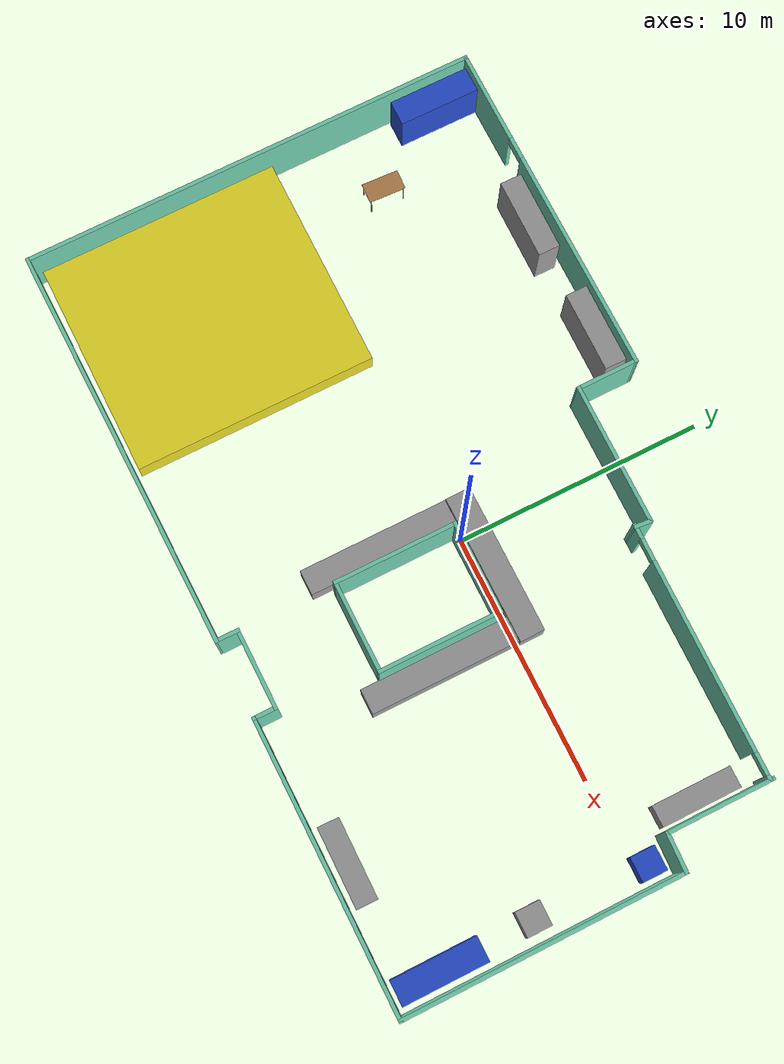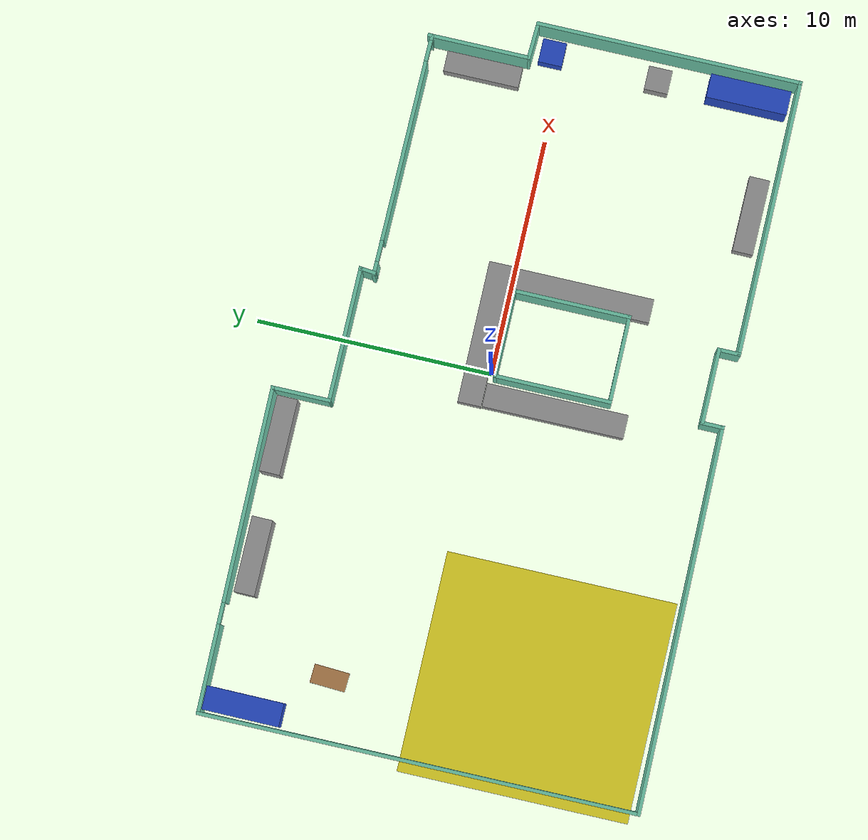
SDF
<sdf version="1.7">
 <world name="lab_arm_world">
  <gravity>0 0 -9.8</gravity>
  <physics name="1ms" type="ignored">
   <max_step_size>0.001</max_step_size>
   <real_time_factor>1</real_time_factor>
   <real_time_update_rate>1000</real_time_update_rate>
  </physics>
  <plugin name="ignition::gazebo::systems::Physics" filename="libignition-gazebo-physics-system.so"/>
  <plugin name="ignition::gazebo::systems::UserCommands" filename="libignition-gazebo-user-commands-system.so"/>
  <plugin name="ignition::gazebo::systems::SceneBroadcaster" filename="libignition-gazebo-scene-broadcaster-system.so"/>
  <plugin name="ignition::gazebo::systems::Imu" filename="libignition-gazebo-imu-system.so"/>
  <plugin name="ignition::gazebo::systems::Sensors" filename="ignition-gazebo-sensors-system">
   <render_engine>ogre2</render_engine>
  </plugin>
  <scene><ambient>0.4 0.4 0.4 1</ambient><background>0.7 0.7 0.7 1</background><shadows>1</shadows></scene>
  <light name="sun" type="directional">
   <cast_shadows>0</cast_shadows>
   <pose>-5 -3 10 0 -0 0</pose>
   <diffuse>1 1 1 1</diffuse>
   <specular>1 1 1 1</specular>
   <direction>0 0 -1</direction>
   <attenuation><range>10</range></attenuation>
   <spot><inner_angle>0</inner_angle><outer_angle>0</outer_angle><falloff>0</falloff></spot>
  </light>
  <magnetic_field>6e-06 2.3e-05 -4.2e-05</magnetic_field>
  <atmosphere type="adiabatic"/>
  <model name="ground_plane">
   <static>1</static>
   <link name="link_ground_plane">
    <collision name="collision">
     <geometry><plane><normal>0 0 1</normal><size>10 10</size></plane></geometry>
    </collision>
   </link>
  </model>
  <model name="RAH-lab">
   <link name="Wall_0">
    <pose>-15.4096 -0.034118 0 0 0 -1.5708</pose>
    <visual name="Wall_0_Visual">
     <pose>0 0 1.25 0 -0 0</pose>
     <geometry><box><size>18.5837 0.15 2.5</size></box></geometry>
     <material>
      <diffuse>0.435294 0.796078 0.67451 1</diffuse>
      <specular>0.1 0.1 0.1 1</specular>
      <ambient>0.435294 0.796078 0.67451 1</ambient>
      <shader type="pixel"/>
     </material>
     <meta><layer>0</layer></meta>
    </visual>
    <collision name="Wall_0_Collision">
     <pose>0 0 1.25 0 -0 0</pose>
     <geometry><box><size>18.5837 0.15 2.5</size></box></geometry>
     <surface>
      <friction>
       <ode><mu>1</mu><mu2>1</mu2><fdir1>0 0 0</fdir1><slip1>0</slip1><slip2>0</slip2></ode>
       <torsional>
        <coefficient>1</coefficient>
        <patch_radius>0</patch_radius>
        <surface_radius>0</surface_radius>
        <use_patch_radius>1</use_patch_radius>
        <ode><slip>0</slip></ode>
       </torsional>
      </friction>
      <bounce><restitution_coefficient>0</restitution_coefficient><threshold>1e+06</threshold></bounce>
      <contact>
       <collide_without_contact>0</collide_without_contact>
       <collide_without_contact_bitmask>1</collide_without_contact_bitmask>
       <collide_bitmask>1</collide_bitmask>
       <ode>
        <soft_cfm>0</soft_cfm>
        <soft_erp>0.2</soft_erp>
        <kp>1e+13</kp>
        <kd>1</kd>
        <max_vel>0.01</max_vel>
        <min_depth>0</min_depth>
       </ode>
       <bullet>
        <split_impulse>1</split_impulse>
        <split_impulse_penetration_threshold>-0.01</split_impulse_penetration_threshold>
        <soft_cfm>0</soft_cfm>
        <soft_erp>0.2</soft_erp>
        <kp>1e+13</kp>
        <kd>1</kd>
       </bullet>
      </contact>
     </surface>
    </collision>
   </link>
   <link name="Wall_1">
    <pose>-7.31852 -9.1806 0 0 -0 0.008695</pose>
    <visual name="Wall_1_Visual">
     <pose>0 0 1.25 0 -0 0</pose>
     <geometry><box><size>16.3328 0.15 2.5</size></box></geometry>
     <material>
      <diffuse>0.435294 0.796078 0.67451 1</diffuse>
      <specular>0.1 0.1 0.1 1</specular>
      <ambient>0.435294 0.796078 0.67451 1</ambient>
      <shader type="pixel"/>
     </material>
     <meta><layer>0</layer></meta>
    </visual>
    <collision name="Wall_1_Collision">
     <pose>0 0 1.25 0 -0 0</pose>
     <geometry><box><size>16.3328 0.15 2.5</size></box></geometry>
     <surface>
      <friction>
       <ode><mu>1</mu><mu2>1</mu2><fdir1>0 0 0</fdir1><slip1>0</slip1><slip2>0</slip2></ode>
       <torsional>
        <coefficient>1</coefficient>
        <patch_radius>0</patch_radius>
        <surface_radius>0</surface_radius>
        <use_patch_radius>1</use_patch_radius>
        <ode><slip>0</slip></ode>
       </torsional>
      </friction>
      <bounce><restitution_coefficient>0</restitution_coefficient><threshold>1e+06</threshold></bounce>
      <contact>
       <collide_without_contact>0</collide_without_contact>
       <collide_without_contact_bitmask>1</collide_without_contact_bitmask>
       <collide_bitmask>1</collide_bitmask>
       <ode>
        <soft_cfm>0</soft_cfm>
        <soft_erp>0.2</soft_erp>
        <kp>1e+13</kp>
        <kd>1</kd>
        <max_vel>0.01</max_vel>
        <min_depth>0</min_depth>
       </ode>
       <bullet>
        <split_impulse>1</split_impulse>
        <split_impulse_penetration_threshold>-0.01</split_impulse_penetration_threshold>
        <soft_cfm>0</soft_cfm>
        <soft_erp>0.2</soft_erp>
        <kp>1e+13</kp>
        <kd>1</kd>
       </bullet>
      </contact>
     </surface>
    </collision>
   </link>
   <link name="Wall_10">
    <pose>3.82389 6.55251 0 0 -0 1.47981</pose>
    <visual name="Wall_10_Visual">
     <pose>0 0 1.25 0 -0 0</pose>
     <geometry><box><size>0.732199 0.15 2.5</size></box></geometry>
     <material>
      <diffuse>0.435294 0.796078 0.67451 1</diffuse>
      <specular>0.1 0.1 0.1 1</specular>
      <ambient>0.435294 0.796078 0.67451 1</ambient>
      <shader type="pixel"/>
     </material>
     <meta><layer>0</layer></meta>
    </visual>
    <collision name="Wall_10_Collision">
     <pose>0 0 1.25 0 -0 0</pose>
     <geometry><box><size>0.732199 0.15 2.5</size></box></geometry>
     <surface>
      <friction>
       <ode><mu>1</mu><mu2>1</mu2><fdir1>0 0 0</fdir1><slip1>0</slip1><slip2>0</slip2></ode>
       <torsional>
        <coefficient>1</coefficient>
        <patch_radius>0</patch_radius>
        <surface_radius>0</surface_radius>
        <use_patch_radius>1</use_patch_radius>
        <ode><slip>0</slip></ode>
       </torsional>
      </friction>
      <bounce><restitution_coefficient>0</restitution_coefficient><threshold>1e+06</threshold></bounce>
      <contact>
       <collide_without_contact>0</collide_without_contact>
       <collide_without_contact_bitmask>1</collide_without_contact_bitmask>
       <collide_bitmask>1</collide_bitmask>
       <ode>
        <soft_cfm>0</soft_cfm>
        <soft_erp>0.2</soft_erp>
        <kp>1e+13</kp>
        <kd>1</kd>
        <max_vel>0.01</max_vel>
        <min_depth>0</min_depth>
       </ode>
       <bullet>
        <split_impulse>1</split_impulse>
        <split_impulse_penetration_threshold>-0.01</split_impulse_penetration_threshold>
        <soft_cfm>0</soft_cfm>
        <soft_erp>0.2</soft_erp>
        <kp>1e+13</kp>
        <kd>1</kd>
       </bullet>
      </contact>
     </surface>
    </collision>
   </link>
   <link name="Wall_11">
    <pose>1.02612 6.85661 0 0 -0 3.13647</pose>
    <visual name="Wall_11_Visual">
     <pose>0 0 1.25 0 -0 0</pose>
     <geometry><box><size>5.69272 0.15 2.5</size></box></geometry>
     <material>
      <diffuse>0.435294 0.796078 0.67451 1</diffuse>
      <specular>0.1 0.1 0.1 1</specular>
      <ambient>0.435294 0.796078 0.67451 1</ambient>
      <shader type="pixel"/>
     </material>
     <meta><layer>0</layer></meta>
    </visual>
    <collision name="Wall_11_Collision">
     <pose>0 0 1.25 0 -0 0</pose>
     <geometry><box><size>5.69272 0.15 2.5</size></box></geometry>
     <surface>
      <friction>
       <ode><mu>1</mu><mu2>1</mu2><fdir1>0 0 0</fdir1><slip1>0</slip1><slip2>0</slip2></ode>
       <torsional>
        <coefficient>1</coefficient>
        <patch_radius>0</patch_radius>
        <surface_radius>0</surface_radius>
        <use_patch_radius>1</use_patch_radius>
        <ode><slip>0</slip></ode>
       </torsional>
      </friction>
      <bounce><restitution_coefficient>0</restitution_coefficient><threshold>1e+06</threshold></bounce>
      <contact>
       <collide_without_contact>0</collide_without_contact>
       <collide_without_contact_bitmask>1</collide_without_contact_bitmask>
       <collide_bitmask>1</collide_bitmask>
       <ode>
        <soft_cfm>0</soft_cfm>
        <soft_erp>0.2</soft_erp>
        <kp>1e+13</kp>
        <kd>1</kd>
        <max_vel>0.01</max_vel>
        <min_depth>0</min_depth>
       </ode>
       <bullet>
        <split_impulse>1</split_impulse>
        <split_impulse_penetration_threshold>-0.01</split_impulse_penetration_threshold>
        <soft_cfm>0</soft_cfm>
        <soft_erp>0.2</soft_erp>
        <kp>1e+13</kp>
        <kd>1</kd>
       </bullet>
      </contact>
     </surface>
    </collision>
   </link>
   <link name="Wall_12">
    <pose>-1.7452 8.04581 0 0 -0 1.5708</pose>
    <visual name="Wall_12_Visual">
     <pose>0 0 1.25 0 -0 0</pose>
     <geometry><box><size>2.5 0.15 2.5</size></box></geometry>
     <material>
      <diffuse>0.435294 0.796078 0.67451 1</diffuse>
      <specular>0.1 0.1 0.1 1</specular>
      <ambient>0.435294 0.796078 0.67451 1</ambient>
      <shader type="pixel"/>
     </material>
     <meta><layer>0</layer></meta>
    </visual>
    <collision name="Wall_12_Collision">
     <pose>0 0 1.25 0 -0 0</pose>
     <geometry><box><size>2.5 0.15 2.5</size></box></geometry>
     <surface>
      <friction>
       <ode><mu>1</mu><mu2>1</mu2><fdir1>0 0 0</fdir1><slip1>0</slip1><slip2>0</slip2></ode>
       <torsional>
        <coefficient>1</coefficient>
        <patch_radius>0</patch_radius>
        <surface_radius>0</surface_radius>
        <use_patch_radius>1</use_patch_radius>
        <ode><slip>0</slip></ode>
       </torsional>
      </friction>
      <bounce><restitution_coefficient>0</restitution_coefficient><threshold>1e+06</threshold></bounce>
      <contact>
       <collide_without_contact>0</collide_without_contact>
       <collide_without_contact_bitmask>1</collide_without_contact_bitmask>
       <collide_bitmask>1</collide_bitmask>
       <ode>
        <soft_cfm>0</soft_cfm>
        <soft_erp>0.2</soft_erp>
        <kp>1e+13</kp>
        <kd>1</kd>
        <max_vel>0.01</max_vel>
        <min_depth>0</min_depth>
       </ode>
       <bullet>
        <split_impulse>1</split_impulse>
        <split_impulse_penetration_threshold>-0.01</split_impulse_penetration_threshold>
        <soft_cfm>0</soft_cfm>
        <soft_erp>0.2</soft_erp>
        <kp>1e+13</kp>
        <kd>1</kd>
       </bullet>
      </contact>
     </surface>
    </collision>
   </link>
   <link name="Wall_13">
    <pose>-8.547 9.21697 0 0 0 -3.13656</pose>
    <visual name="Wall_13_Visual_1">
     <pose>5.00383 0 1.25 0 -0 0</pose>
     <geometry><box><size>3.74618 0.15 2.5</size></box></geometry>
     <material>
      <diffuse>0.435294 0.796078 0.67451 1</diffuse>
      <specular>0.1 0.1 0.1 1</specular>
      <ambient>0.435294 0.796078 0.67451 1</ambient>
      <shader type="pixel"/>
     </material>
     <meta><layer>0</layer></meta>
    </visual>
    <visual name="Wall_13_Visual_2">
     <pose>2.68074 0 2.25 0 -0 0</pose>
     <geometry><box><size>0.9 0.15 0.5</size></box></geometry>
     <material>
      <diffuse>0.435294 0.796078 0.67451 1</diffuse>
      <specular>0.1 0.1 0.1 1</specular>
      <ambient>0.435294 0.796078 0.67451 1</ambient>
      <shader type="pixel"/>
     </material>
     <meta><layer>0</layer></meta>
    </visual>
    <visual name="Wall_13_Visual_0">
     <pose>-2.32309 0 1.25 0 -0 0</pose>
     <geometry><box><size>9.10767 0.15 2.5</size></box></geometry>
     <material>
      <diffuse>0.435294 0.796078 0.67451 1</diffuse>
      <specular>0.1 0.1 0.1 1</specular>
      <ambient>0.435294 0.796078 0.67451 1</ambient>
      <shader type="pixel"/>
     </material>
     <meta><layer>0</layer></meta>
    </visual>
    <collision name="Wall_13_Collision_0">
     <pose>-2.32309 0 1.25 0 -0 0</pose>
     <geometry><box><size>9.10767 0.15 2.5</size></box></geometry>
     <surface>
      <friction>
       <ode><mu>1</mu><mu2>1</mu2><fdir1>0 0 0</fdir1><slip1>0</slip1><slip2>0</slip2></ode>
       <torsional>
        <coefficient>1</coefficient>
        <patch_radius>0</patch_radius>
        <surface_radius>0</surface_radius>
        <use_patch_radius>1</use_patch_radius>
        <ode><slip>0</slip></ode>
       </torsional>
      </friction>
      <bounce><restitution_coefficient>0</restitution_coefficient><threshold>1e+06</threshold></bounce>
      <contact>
       <collide_without_contact>0</collide_without_contact>
       <collide_without_contact_bitmask>1</collide_without_contact_bitmask>
       <collide_bitmask>1</collide_bitmask>
       <ode>
        <soft_cfm>0</soft_cfm>
        <soft_erp>0.2</soft_erp>
        <kp>1e+13</kp>
        <kd>1</kd>
        <max_vel>0.01</max_vel>
        <min_depth>0</min_depth>
       </ode>
       <bullet>
        <split_impulse>1</split_impulse>
        <split_impulse_penetration_threshold>-0.01</split_impulse_penetration_threshold>
        <soft_cfm>0</soft_cfm>
        <soft_erp>0.2</soft_erp>
        <kp>1e+13</kp>
        <kd>1</kd>
       </bullet>
      </contact>
     </surface>
    </collision>
    <collision name="Wall_13_Collision_2">
     <pose>2.68074 0 2.25 0 -0 0</pose>
     <geometry><box><size>0.9 0.15 0.5</size></box></geometry>
     <surface>
      <friction>
       <ode><mu>1</mu><mu2>1</mu2><fdir1>0 0 0</fdir1><slip1>0</slip1><slip2>0</slip2></ode>
       <torsional>
        <coefficient>1</coefficient>
        <patch_radius>0</patch_radius>
        <surface_radius>0</surface_radius>
        <use_patch_radius>1</use_patch_radius>
        <ode><slip>0</slip></ode>
       </torsional>
      </friction>
      <bounce><restitution_coefficient>0</restitution_coefficient><threshold>1e+06</threshold></bounce>
      <contact>
       <collide_without_contact>0</collide_without_contact>
       <collide_without_contact_bitmask>1</collide_without_contact_bitmask>
       <collide_bitmask>1</collide_bitmask>
       <ode>
        <soft_cfm>0</soft_cfm>
        <soft_erp>0.2</soft_erp>
        <kp>1e+13</kp>
        <kd>1</kd>
        <max_vel>0.01</max_vel>
        <min_depth>0</min_depth>
       </ode>
       <bullet>
        <split_impulse>1</split_impulse>
        <split_impulse_penetration_threshold>-0.01</split_impulse_penetration_threshold>
        <soft_cfm>0</soft_cfm>
        <soft_erp>0.2</soft_erp>
        <kp>1e+13</kp>
        <kd>1</kd>
       </bullet>
      </contact>
     </surface>
    </collision>
    <collision name="Wall_13_Collision_1">
     <pose>5.00383 0 1.25 0 -0 0</pose>
     <geometry><box><size>3.74618 0.15 2.5</size></box></geometry>
     <surface>
      <friction>
       <ode><mu>1</mu><mu2>1</mu2><fdir1>0 0 0</fdir1><slip1>0</slip1><slip2>0</slip2></ode>
       <torsional>
        <coefficient>1</coefficient>
        <patch_radius>0</patch_radius>
        <surface_radius>0</surface_radius>
        <use_patch_radius>1</use_patch_radius>
        <ode><slip>0</slip></ode>
       </torsional>
      </friction>
      <bounce><restitution_coefficient>0</restitution_coefficient><threshold>1e+06</threshold></bounce>
      <contact>
       <collide_without_contact>0</collide_without_contact>
       <collide_without_contact_bitmask>1</collide_without_contact_bitmask>
       <collide_bitmask>1</collide_bitmask>
       <ode>
        <soft_cfm>0</soft_cfm>
        <soft_erp>0.2</soft_erp>
        <kp>1e+13</kp>
        <kd>1</kd>
        <max_vel>0.01</max_vel>
        <min_depth>0</min_depth>
       </ode>
       <bullet>
        <split_impulse>1</split_impulse>
        <split_impulse_penetration_threshold>-0.01</split_impulse_penetration_threshold>
        <soft_cfm>0</soft_cfm>
        <soft_erp>0.2</soft_erp>
        <kp>1e+13</kp>
        <kd>1</kd>
       </bullet>
      </contact>
     </surface>
    </collision>
   </link>
   <link name="Wall_15">
    <pose>0.761931 -1.9537 0 0 0 -1.5708</pose>
    <visual name="Wall_15_Visual">
     <pose>0 0 1.25 0 -0 0</pose>
     <geometry><box><size>5 0.15 2.5</size></box></geometry>
     <material>
      <diffuse>0.435294 0.796078 0.67451 1</diffuse>
      <specular>0.1 0.1 0.1 1</specular>
      <ambient>0.435294 0.796078 0.67451 1</ambient>
      <shader type="pixel"/>
     </material>
     <meta><layer>0</layer></meta>
    </visual>
    <collision name="Wall_15_Collision">
     <pose>0 0 1.25 0 -0 0</pose>
     <geometry><box><size>5 0.15 2.5</size></box></geometry>
     <surface>
      <friction>
       <ode><mu>1</mu><mu2>1</mu2><fdir1>0 0 0</fdir1><slip1>0</slip1><slip2>0</slip2></ode>
       <torsional>
        <coefficient>1</coefficient>
        <patch_radius>0</patch_radius>
        <surface_radius>0</surface_radius>
        <use_patch_radius>1</use_patch_radius>
        <ode><slip>0</slip></ode>
       </torsional>
      </friction>
      <bounce><restitution_coefficient>0</restitution_coefficient><threshold>1e+06</threshold></bounce>
      <contact>
       <collide_without_contact>0</collide_without_contact>
       <collide_without_contact_bitmask>1</collide_without_contact_bitmask>
       <collide_bitmask>1</collide_bitmask>
       <ode>
        <soft_cfm>0</soft_cfm>
        <soft_erp>0.2</soft_erp>
        <kp>1e+13</kp>
        <kd>1</kd>
        <max_vel>0.01</max_vel>
        <min_depth>0</min_depth>
       </ode>
       <bullet>
        <split_impulse>1</split_impulse>
        <split_impulse_penetration_threshold>-0.01</split_impulse_penetration_threshold>
        <soft_cfm>0</soft_cfm>
        <soft_erp>0.2</soft_erp>
        <kp>1e+13</kp>
        <kd>1</kd>
       </bullet>
      </contact>
     </surface>
    </collision>
   </link>
   <link name="Wall_16">
    <pose>2.56193 -4.3787 0 0 -0 0</pose>
    <visual name="Wall_16_Visual">
     <pose>0 0 1.25 0 -0 0</pose>
     <geometry><box><size>3.75 0.15 2.5</size></box></geometry>
     <material>
      <diffuse>0.435294 0.796078 0.67451 1</diffuse>
      <specular>0.1 0.1 0.1 1</specular>
      <ambient>0.435294 0.796078 0.67451 1</ambient>
      <shader type="pixel"/>
     </material>
     <meta><layer>0</layer></meta>
    </visual>
    <collision name="Wall_16_Collision">
     <pose>0 0 1.25 0 -0 0</pose>
     <geometry><box><size>3.75 0.15 2.5</size></box></geometry>
     <surface>
      <friction>
       <ode><mu>1</mu><mu2>1</mu2><fdir1>0 0 0</fdir1><slip1>0</slip1><slip2>0</slip2></ode>
       <torsional>
        <coefficient>1</coefficient>
        <patch_radius>0</patch_radius>
        <surface_radius>0</surface_radius>
        <use_patch_radius>1</use_patch_radius>
        <ode><slip>0</slip></ode>
       </torsional>
      </friction>
      <bounce><restitution_coefficient>0</restitution_coefficient><threshold>1e+06</threshold></bounce>
      <contact>
       <collide_without_contact>0</collide_without_contact>
       <collide_without_contact_bitmask>1</collide_without_contact_bitmask>
       <collide_bitmask>1</collide_bitmask>
       <ode>
        <soft_cfm>0</soft_cfm>
        <soft_erp>0.2</soft_erp>
        <kp>1e+13</kp>
        <kd>1</kd>
        <max_vel>0.01</max_vel>
        <min_depth>0</min_depth>
       </ode>
       <bullet>
        <split_impulse>1</split_impulse>
        <split_impulse_penetration_threshold>-0.01</split_impulse_penetration_threshold>
        <soft_cfm>0</soft_cfm>
        <soft_erp>0.2</soft_erp>
        <kp>1e+13</kp>
        <kd>1</kd>
       </bullet>
      </contact>
     </surface>
    </collision>
   </link>
   <link name="Wall_17">
    <pose>4.36193 -1.9537 0 0 -0 1.5708</pose>
    <visual name="Wall_17_Visual">
     <pose>0 0 1.25 0 -0 0</pose>
     <geometry><box><size>5 0.15 2.5</size></box></geometry>
     <material>
      <diffuse>0.435294 0.796078 0.67451 1</diffuse>
      <specular>0.1 0.1 0.1 1</specular>
      <ambient>0.435294 0.796078 0.67451 1</ambient>
      <shader type="pixel"/>
     </material>
     <meta><layer>0</layer></meta>
    </visual>
    <collision name="Wall_17_Collision">
     <pose>0 0 1.25 0 -0 0</pose>
     <geometry><box><size>5 0.15 2.5</size></box></geometry>
     <surface>
      <friction>
       <ode><mu>1</mu><mu2>1</mu2><fdir1>0 0 0</fdir1><slip1>0</slip1><slip2>0</slip2></ode>
       <torsional>
        <coefficient>1</coefficient>
        <patch_radius>0</patch_radius>
        <surface_radius>0</surface_radius>
        <use_patch_radius>1</use_patch_radius>
        <ode><slip>0</slip></ode>
       </torsional>
      </friction>
      <bounce><restitution_coefficient>0</restitution_coefficient><threshold>1e+06</threshold></bounce>
      <contact>
       <collide_without_contact>0</collide_without_contact>
       <collide_without_contact_bitmask>1</collide_without_contact_bitmask>
       <collide_bitmask>1</collide_bitmask>
       <ode>
        <soft_cfm>0</soft_cfm>
        <soft_erp>0.2</soft_erp>
        <kp>1e+13</kp>
        <kd>1</kd>
        <max_vel>0.01</max_vel>
        <min_depth>0</min_depth>
       </ode>
       <bullet>
        <split_impulse>1</split_impulse>
        <split_impulse_penetration_threshold>-0.01</split_impulse_penetration_threshold>
        <soft_cfm>0</soft_cfm>
        <soft_erp>0.2</soft_erp>
        <kp>1e+13</kp>
        <kd>1</kd>
       </bullet>
      </contact>
     </surface>
    </collision>
   </link>
   <link name="Wall_18">
    <pose>2.56193 0.471296 0 0 -0 3.14159</pose>
    <visual name="Wall_18_Visual">
     <pose>0 0 1.25 0 -0 0</pose>
     <geometry><box><size>3.75 0.15 2.5</size></box></geometry>
     <material>
      <diffuse>0.435294 0.796078 0.67451 1</diffuse>
      <specular>0.1 0.1 0.1 1</specular>
      <ambient>0.435294 0.796078 0.67451 1</ambient>
      <shader type="pixel"/>
     </material>
     <meta><layer>0</layer></meta>
    </visual>
    <collision name="Wall_18_Collision">
     <pose>0 0 1.25 0 -0 0</pose>
     <geometry><box><size>3.75 0.15 2.5</size></box></geometry>
     <surface>
      <friction>
       <ode><mu>1</mu><mu2>1</mu2><fdir1>0 0 0</fdir1><slip1>0</slip1><slip2>0</slip2></ode>
       <torsional>
        <coefficient>1</coefficient>
        <patch_radius>0</patch_radius>
        <surface_radius>0</surface_radius>
        <use_patch_radius>1</use_patch_radius>
        <ode><slip>0</slip></ode>
       </torsional>
      </friction>
      <bounce><restitution_coefficient>0</restitution_coefficient><threshold>1e+06</threshold></bounce>
      <contact>
       <collide_without_contact>0</collide_without_contact>
       <collide_without_contact_bitmask>1</collide_without_contact_bitmask>
       <collide_bitmask>1</collide_bitmask>
       <ode>
        <soft_cfm>0</soft_cfm>
        <soft_erp>0.2</soft_erp>
        <kp>1e+13</kp>
        <kd>1</kd>
        <max_vel>0.01</max_vel>
        <min_depth>0</min_depth>
       </ode>
       <bullet>
        <split_impulse>1</split_impulse>
        <split_impulse_penetration_threshold>-0.01</split_impulse_penetration_threshold>
        <soft_cfm>0</soft_cfm>
        <soft_erp>0.2</soft_erp>
        <kp>1e+13</kp>
        <kd>1</kd>
       </bullet>
      </contact>
     </surface>
    </collision>
   </link>
   <link name="Wall_2">
    <pose>0.772595 -8.68809 0 0 -0 1.5708</pose>
    <visual name="Wall_2_Visual">
     <pose>0 0 1.25 0 -0 0</pose>
     <geometry><box><size>0.99429 0.15 2.5</size></box></geometry>
     <material>
      <diffuse>0.435294 0.796078 0.67451 1</diffuse>
      <specular>0.1 0.1 0.1 1</specular>
      <ambient>0.435294 0.796078 0.67451 1</ambient>
      <shader type="pixel"/>
     </material>
     <meta><layer>0</layer></meta>
    </visual>
    <collision name="Wall_2_Collision">
     <pose>0 0 1.25 0 -0 0</pose>
     <geometry><box><size>0.99429 0.15 2.5</size></box></geometry>
     <surface>
      <friction>
       <ode><mu>1</mu><mu2>1</mu2><fdir1>0 0 0</fdir1><slip1>0</slip1><slip2>0</slip2></ode>
       <torsional>
        <coefficient>1</coefficient>
        <patch_radius>0</patch_radius>
        <surface_radius>0</surface_radius>
        <use_patch_radius>1</use_patch_radius>
        <ode><slip>0</slip></ode>
       </torsional>
      </friction>
      <bounce><restitution_coefficient>0</restitution_coefficient><threshold>1e+06</threshold></bounce>
      <contact>
       <collide_without_contact>0</collide_without_contact>
       <collide_without_contact_bitmask>1</collide_without_contact_bitmask>
       <collide_bitmask>1</collide_bitmask>
       <ode>
        <soft_cfm>0</soft_cfm>
        <soft_erp>0.2</soft_erp>
        <kp>1e+13</kp>
        <kd>1</kd>
        <max_vel>0.01</max_vel>
        <min_depth>0</min_depth>
       </ode>
       <bullet>
        <split_impulse>1</split_impulse>
        <split_impulse_penetration_threshold>-0.01</split_impulse_penetration_threshold>
        <soft_cfm>0</soft_cfm>
        <soft_erp>0.2</soft_erp>
        <kp>1e+13</kp>
        <kd>1</kd>
       </bullet>
      </contact>
     </surface>
    </collision>
   </link>
   <link name="Wall_3">
    <pose>2.32046 -8.26595 0 0 -0 0</pose>
    <visual name="Wall_3_Visual">
     <pose>0 0 1.25 0 -0 0</pose>
     <geometry><box><size>3.24573 0.15 2.5</size></box></geometry>
     <material>
      <diffuse>0.435294 0.796078 0.67451 1</diffuse>
      <specular>0.1 0.1 0.1 1</specular>
      <ambient>0.435294 0.796078 0.67451 1</ambient>
      <shader type="pixel"/>
     </material>
     <meta><layer>0</layer></meta>
    </visual>
    <collision name="Wall_3_Collision">
     <pose>0 0 1.25 0 -0 0</pose>
     <geometry><box><size>3.24573 0.15 2.5</size></box></geometry>
     <surface>
      <friction>
       <ode><mu>1</mu><mu2>1</mu2><fdir1>0 0 0</fdir1><slip1>0</slip1><slip2>0</slip2></ode>
       <torsional>
        <coefficient>1</coefficient>
        <patch_radius>0</patch_radius>
        <surface_radius>0</surface_radius>
        <use_patch_radius>1</use_patch_radius>
        <ode><slip>0</slip></ode>
       </torsional>
      </friction>
      <bounce><restitution_coefficient>0</restitution_coefficient><threshold>1e+06</threshold></bounce>
      <contact>
       <collide_without_contact>0</collide_without_contact>
       <collide_without_contact_bitmask>1</collide_without_contact_bitmask>
       <collide_bitmask>1</collide_bitmask>
       <ode>
        <soft_cfm>0</soft_cfm>
        <soft_erp>0.2</soft_erp>
        <kp>1e+13</kp>
        <kd>1</kd>
        <max_vel>0.01</max_vel>
        <min_depth>0</min_depth>
       </ode>
       <bullet>
        <split_impulse>1</split_impulse>
        <split_impulse_penetration_threshold>-0.01</split_impulse_penetration_threshold>
        <soft_cfm>0</soft_cfm>
        <soft_erp>0.2</soft_erp>
        <kp>1e+13</kp>
        <kd>1</kd>
       </bullet>
      </contact>
     </surface>
    </collision>
   </link>
   <link name="Wall_4">
    <pose>3.86833 -8.68809 0 0 0 -1.5708</pose>
    <visual name="Wall_4_Visual">
     <pose>0 0 1.25 0 -0 0</pose>
     <geometry><box><size>0.99429 0.15 2.5</size></box></geometry>
     <material>
      <diffuse>0.435294 0.796078 0.67451 1</diffuse>
      <specular>0.1 0.1 0.1 1</specular>
      <ambient>0.435294 0.796078 0.67451 1</ambient>
      <shader type="pixel"/>
     </material>
     <meta><layer>0</layer></meta>
    </visual>
    <collision name="Wall_4_Collision">
     <pose>0 0 1.25 0 -0 0</pose>
     <geometry><box><size>0.99429 0.15 2.5</size></box></geometry>
     <surface>
      <friction>
       <ode><mu>1</mu><mu2>1</mu2><fdir1>0 0 0</fdir1><slip1>0</slip1><slip2>0</slip2></ode>
       <torsional>
        <coefficient>1</coefficient>
        <patch_radius>0</patch_radius>
        <surface_radius>0</surface_radius>
        <use_patch_radius>1</use_patch_radius>
        <ode><slip>0</slip></ode>
       </torsional>
      </friction>
      <bounce><restitution_coefficient>0</restitution_coefficient><threshold>1e+06</threshold></bounce>
      <contact>
       <collide_without_contact>0</collide_without_contact>
       <collide_without_contact_bitmask>1</collide_without_contact_bitmask>
       <collide_bitmask>1</collide_bitmask>
       <ode>
        <soft_cfm>0</soft_cfm>
        <soft_erp>0.2</soft_erp>
        <kp>1e+13</kp>
        <kd>1</kd>
        <max_vel>0.01</max_vel>
        <min_depth>0</min_depth>
       </ode>
       <bullet>
        <split_impulse>1</split_impulse>
        <split_impulse_penetration_threshold>-0.01</split_impulse_penetration_threshold>
        <soft_cfm>0</soft_cfm>
        <soft_erp>0.2</soft_erp>
        <kp>1e+13</kp>
        <kd>1</kd>
       </bullet>
      </contact>
     </surface>
    </collision>
   </link>
   <link name="Wall_5">
    <pose>9.63764 -9.11024 0 0 -0 0</pose>
    <visual name="Wall_5_Visual">
     <pose>0 0 1.25 0 -0 0</pose>
     <geometry><box><size>11.6886 0.15 2.5</size></box></geometry>
     <material>
      <diffuse>0.435294 0.796078 0.67451 1</diffuse>
      <specular>0.1 0.1 0.1 1</specular>
      <ambient>0.435294 0.796078 0.67451 1</ambient>
      <shader type="pixel"/>
     </material>
     <meta><layer>0</layer></meta>
    </visual>
    <collision name="Wall_5_Collision">
     <pose>0 0 1.25 0 -0 0</pose>
     <geometry><box><size>11.6886 0.15 2.5</size></box></geometry>
     <surface>
      <friction>
       <ode><mu>1</mu><mu2>1</mu2><fdir1>0 0 0</fdir1><slip1>0</slip1><slip2>0</slip2></ode>
       <torsional>
        <coefficient>1</coefficient>
        <patch_radius>0</patch_radius>
        <surface_radius>0</surface_radius>
        <use_patch_radius>1</use_patch_radius>
        <ode><slip>0</slip></ode>
       </torsional>
      </friction>
      <bounce><restitution_coefficient>0</restitution_coefficient><threshold>1e+06</threshold></bounce>
      <contact>
       <collide_without_contact>0</collide_without_contact>
       <collide_without_contact_bitmask>1</collide_without_contact_bitmask>
       <collide_bitmask>1</collide_bitmask>
       <ode>
        <soft_cfm>0</soft_cfm>
        <soft_erp>0.2</soft_erp>
        <kp>1e+13</kp>
        <kd>1</kd>
        <max_vel>0.01</max_vel>
        <min_depth>0</min_depth>
       </ode>
       <bullet>
        <split_impulse>1</split_impulse>
        <split_impulse_penetration_threshold>-0.01</split_impulse_penetration_threshold>
        <soft_cfm>0</soft_cfm>
        <soft_erp>0.2</soft_erp>
        <kp>1e+13</kp>
        <kd>1</kd>
       </bullet>
      </contact>
     </surface>
    </collision>
   </link>
   <link name="Wall_6">
    <pose>15.407 -3.56024 0 0 -0 1.5708</pose>
    <visual name="Wall_6_Visual">
     <pose>0 0 1.25 0 -0 0</pose>
     <geometry><box><size>11.25 0.15 2.5</size></box></geometry>
     <material>
      <diffuse>0.435294 0.796078 0.67451 1</diffuse>
      <specular>0.1 0.1 0.1 1</specular>
      <ambient>0.435294 0.796078 0.67451 1</ambient>
      <shader type="pixel"/>
     </material>
     <meta><layer>0</layer></meta>
    </visual>
    <collision name="Wall_6_Collision">
     <pose>0 0 1.25 0 -0 0</pose>
     <geometry><box><size>11.25 0.15 2.5</size></box></geometry>
     <surface>
      <friction>
       <ode><mu>1</mu><mu2>1</mu2><fdir1>0 0 0</fdir1><slip1>0</slip1><slip2>0</slip2></ode>
       <torsional>
        <coefficient>1</coefficient>
        <patch_radius>0</patch_radius>
        <surface_radius>0</surface_radius>
        <use_patch_radius>1</use_patch_radius>
        <ode><slip>0</slip></ode>
       </torsional>
      </friction>
      <bounce><restitution_coefficient>0</restitution_coefficient><threshold>1e+06</threshold></bounce>
      <contact>
       <collide_without_contact>0</collide_without_contact>
       <collide_without_contact_bitmask>1</collide_without_contact_bitmask>
       <collide_bitmask>1</collide_bitmask>
       <ode>
        <soft_cfm>0</soft_cfm>
        <soft_erp>0.2</soft_erp>
        <kp>1e+13</kp>
        <kd>1</kd>
        <max_vel>0.01</max_vel>
        <min_depth>0</min_depth>
       </ode>
       <bullet>
        <split_impulse>1</split_impulse>
        <split_impulse_penetration_threshold>-0.01</split_impulse_penetration_threshold>
        <soft_cfm>0</soft_cfm>
        <soft_erp>0.2</soft_erp>
        <kp>1e+13</kp>
        <kd>1</kd>
       </bullet>
      </contact>
     </surface>
    </collision>
   </link>
   <link name="Wall_7">
    <pose>14.6685 2.02329 0 0 -0 3.09622</pose>
    <visual name="Wall_7_Visual">
     <pose>0 0 1.25 0 -0 0</pose>
     <geometry><box><size>1.6285 0.15 2.5</size></box></geometry>
     <material>
      <diffuse>0.435294 0.796078 0.67451 1</diffuse>
      <specular>0.1 0.1 0.1 1</specular>
      <ambient>0.435294 0.796078 0.67451 1</ambient>
      <shader type="pixel"/>
     </material>
     <meta><layer>0</layer></meta>
    </visual>
    <collision name="Wall_7_Collision">
     <pose>0 0 1.25 0 -0 0</pose>
     <geometry><box><size>1.6285 0.15 2.5</size></box></geometry>
     <surface>
      <friction>
       <ode><mu>1</mu><mu2>1</mu2><fdir1>0 0 0</fdir1><slip1>0</slip1><slip2>0</slip2></ode>
       <torsional>
        <coefficient>1</coefficient>
        <patch_radius>0</patch_radius>
        <surface_radius>0</surface_radius>
        <use_patch_radius>1</use_patch_radius>
        <ode><slip>0</slip></ode>
       </torsional>
      </friction>
      <bounce><restitution_coefficient>0</restitution_coefficient><threshold>1e+06</threshold></bounce>
      <contact>
       <collide_without_contact>0</collide_without_contact>
       <collide_without_contact_bitmask>1</collide_without_contact_bitmask>
       <collide_bitmask>1</collide_bitmask>
       <ode>
        <soft_cfm>0</soft_cfm>
        <soft_erp>0.2</soft_erp>
        <kp>1e+13</kp>
        <kd>1</kd>
        <max_vel>0.01</max_vel>
        <min_depth>0</min_depth>
       </ode>
       <bullet>
        <split_impulse>1</split_impulse>
        <split_impulse_penetration_threshold>-0.01</split_impulse_penetration_threshold>
        <soft_cfm>0</soft_cfm>
        <soft_erp>0.2</soft_erp>
        <kp>1e+13</kp>
        <kd>1</kd>
       </bullet>
      </contact>
     </surface>
    </collision>
   </link>
   <link name="Wall_8">
    <pose>13.93 4.21262 0 0 -0 1.5708</pose>
    <visual name="Wall_8_Visual">
     <pose>0 0 1.25 0 -0 0</pose>
     <geometry><box><size>4.25 0.15 2.5</size></box></geometry>
     <material>
      <diffuse>0.435294 0.796078 0.67451 1</diffuse>
      <specular>0.1 0.1 0.1 1</specular>
      <ambient>0.435294 0.796078 0.67451 1</ambient>
      <shader type="pixel"/>
     </material>
     <meta><layer>0</layer></meta>
    </visual>
    <collision name="Wall_8_Collision">
     <pose>0 0 1.25 0 -0 0</pose>
     <geometry><box><size>4.25 0.15 2.5</size></box></geometry>
     <surface>
      <friction>
       <ode><mu>1</mu><mu2>1</mu2><fdir1>0 0 0</fdir1><slip1>0</slip1><slip2>0</slip2></ode>
       <torsional>
        <coefficient>1</coefficient>
        <patch_radius>0</patch_radius>
        <surface_radius>0</surface_radius>
        <use_patch_radius>1</use_patch_radius>
        <ode><slip>0</slip></ode>
       </torsional>
      </friction>
      <bounce><restitution_coefficient>0</restitution_coefficient><threshold>1e+06</threshold></bounce>
      <contact>
       <collide_without_contact>0</collide_without_contact>
       <collide_without_contact_bitmask>1</collide_without_contact_bitmask>
       <collide_bitmask>1</collide_bitmask>
       <ode>
        <soft_cfm>0</soft_cfm>
        <soft_erp>0.2</soft_erp>
        <kp>1e+13</kp>
        <kd>1</kd>
        <max_vel>0.01</max_vel>
        <min_depth>0</min_depth>
       </ode>
       <bullet>
        <split_impulse>1</split_impulse>
        <split_impulse_penetration_threshold>-0.01</split_impulse_penetration_threshold>
        <soft_cfm>0</soft_cfm>
        <soft_erp>0.2</soft_erp>
        <kp>1e+13</kp>
        <kd>1</kd>
       </bullet>
      </contact>
     </surface>
    </collision>
   </link>
   <link name="Wall_9">
    <pose>8.83726 6.20972 0 0 -0 3.13121</pose>
    <visual name="Wall_9_Visual_1">
     <pose>-0.176365 0 1.25 0 -0 0</pose>
     <geometry><box><size>7.65823 0.15 2.5</size></box></geometry>
     <material>
      <diffuse>0.435294 0.796078 0.67451 1</diffuse>
      <specular>0.1 0.1 0.1 1</specular>
      <ambient>0.435294 0.796078 0.67451 1</ambient>
      <shader type="pixel"/>
     </material>
     <meta><layer>0</layer></meta>
    </visual>
    <visual name="Wall_9_Visual_2">
     <pose>4.86037 0 1.25 0 -0 0</pose>
     <geometry><box><size>0.615245 0.15 2.5</size></box></geometry>
     <material>
      <diffuse>0.435294 0.796078 0.67451 1</diffuse>
      <specular>0.1 0.1 0.1 1</specular>
      <ambient>0.435294 0.796078 0.67451 1</ambient>
      <shader type="pixel"/>
     </material>
     <meta><layer>0</layer></meta>
    </visual>
    <visual name="Wall_9_Visual_3">
     <pose>-4.45548 0 2.25 0 -0 0</pose>
     <geometry><box><size>0.9 0.15 0.5</size></box></geometry>
     <material>
      <diffuse>0.435294 0.796078 0.67451 1</diffuse>
      <specular>0.1 0.1 0.1 1</specular>
      <ambient>0.435294 0.796078 0.67451 1</ambient>
      <shader type="pixel"/>
     </material>
     <meta><layer>0</layer></meta>
    </visual>
    <visual name="Wall_9_Visual_4">
     <pose>4.10275 0 2.25 0 -0 0</pose>
     <geometry><box><size>0.9 0.15 0.5</size></box></geometry>
     <material>
      <diffuse>0.435294 0.796078 0.67451 1</diffuse>
      <specular>0.1 0.1 0.1 1</specular>
      <ambient>0.435294 0.796078 0.67451 1</ambient>
      <shader type="pixel"/>
     </material>
     <meta><layer>0</layer></meta>
    </visual>
    <visual name="Wall_9_Visual_0">
     <pose>-5.03674 0 1.25 0 -0 0</pose>
     <geometry><box><size>0.262515 0.15 2.5</size></box></geometry>
     <material>
      <diffuse>0.435294 0.796078 0.67451 1</diffuse>
      <specular>0.1 0.1 0.1 1</specular>
      <ambient>0.435294 0.796078 0.67451 1</ambient>
      <shader type="pixel"/>
     </material>
     <meta><layer>0</layer></meta>
    </visual>
    <collision name="Wall_9_Collision_0">
     <pose>-5.03674 0 1.25 0 -0 0</pose>
     <geometry><box><size>0.262515 0.15 2.5</size></box></geometry>
     <surface>
      <friction>
       <ode><mu>1</mu><mu2>1</mu2><fdir1>0 0 0</fdir1><slip1>0</slip1><slip2>0</slip2></ode>
       <torsional>
        <coefficient>1</coefficient>
        <patch_radius>0</patch_radius>
        <surface_radius>0</surface_radius>
        <use_patch_radius>1</use_patch_radius>
        <ode><slip>0</slip></ode>
       </torsional>
      </friction>
      <bounce><restitution_coefficient>0</restitution_coefficient><threshold>1e+06</threshold></bounce>
      <contact>
       <collide_without_contact>0</collide_without_contact>
       <collide_without_contact_bitmask>1</collide_without_contact_bitmask>
       <collide_bitmask>1</collide_bitmask>
       <ode>
        <soft_cfm>0</soft_cfm>
        <soft_erp>0.2</soft_erp>
        <kp>1e+13</kp>
        <kd>1</kd>
        <max_vel>0.01</max_vel>
        <min_depth>0</min_depth>
       </ode>
       <bullet>
        <split_impulse>1</split_impulse>
        <split_impulse_penetration_threshold>-0.01</split_impulse_penetration_threshold>
        <soft_cfm>0</soft_cfm>
        <soft_erp>0.2</soft_erp>
        <kp>1e+13</kp>
        <kd>1</kd>
       </bullet>
      </contact>
     </surface>
    </collision>
    <collision name="Wall_9_Collision_1">
     <pose>-0.176365 0 1.25 0 -0 0</pose>
     <geometry><box><size>7.65823 0.15 2.5</size></box></geometry>
     <surface>
      <friction>
       <ode><mu>1</mu><mu2>1</mu2><fdir1>0 0 0</fdir1><slip1>0</slip1><slip2>0</slip2></ode>
       <torsional>
        <coefficient>1</coefficient>
        <patch_radius>0</patch_radius>
        <surface_radius>0</surface_radius>
        <use_patch_radius>1</use_patch_radius>
        <ode><slip>0</slip></ode>
       </torsional>
      </friction>
      <bounce><restitution_coefficient>0</restitution_coefficient><threshold>1e+06</threshold></bounce>
      <contact>
       <collide_without_contact>0</collide_without_contact>
       <collide_without_contact_bitmask>1</collide_without_contact_bitmask>
       <collide_bitmask>1</collide_bitmask>
       <ode>
        <soft_cfm>0</soft_cfm>
        <soft_erp>0.2</soft_erp>
        <kp>1e+13</kp>
        <kd>1</kd>
        <max_vel>0.01</max_vel>
        <min_depth>0</min_depth>
       </ode>
       <bullet>
        <split_impulse>1</split_impulse>
        <split_impulse_penetration_threshold>-0.01</split_impulse_penetration_threshold>
        <soft_cfm>0</soft_cfm>
        <soft_erp>0.2</soft_erp>
        <kp>1e+13</kp>
        <kd>1</kd>
       </bullet>
      </contact>
     </surface>
    </collision>
    <collision name="Wall_9_Collision_2">
     <pose>4.86037 0 1.25 0 -0 0</pose>
     <geometry><box><size>0.615245 0.15 2.5</size></box></geometry>
     <surface>
      <friction>
       <ode><mu>1</mu><mu2>1</mu2><fdir1>0 0 0</fdir1><slip1>0</slip1><slip2>0</slip2></ode>
       <torsional>
        <coefficient>1</coefficient>
        <patch_radius>0</patch_radius>
        <surface_radius>0</surface_radius>
        <use_patch_radius>1</use_patch_radius>
        <ode><slip>0</slip></ode>
       </torsional>
      </friction>
      <bounce><restitution_coefficient>0</restitution_coefficient><threshold>1e+06</threshold></bounce>
      <contact>
       <collide_without_contact>0</collide_without_contact>
       <collide_without_contact_bitmask>1</collide_without_contact_bitmask>
       <collide_bitmask>1</collide_bitmask>
       <ode>
        <soft_cfm>0</soft_cfm>
        <soft_erp>0.2</soft_erp>
        <kp>1e+13</kp>
        <kd>1</kd>
        <max_vel>0.01</max_vel>
        <min_depth>0</min_depth>
       </ode>
       <bullet>
        <split_impulse>1</split_impulse>
        <split_impulse_penetration_threshold>-0.01</split_impulse_penetration_threshold>
        <soft_cfm>0</soft_cfm>
        <soft_erp>0.2</soft_erp>
        <kp>1e+13</kp>
        <kd>1</kd>
       </bullet>
      </contact>
     </surface>
    </collision>
    <collision name="Wall_9_Collision_3">
     <pose>-4.45548 0 2.25 0 -0 0</pose>
     <geometry><box><size>0.9 0.15 0.5</size></box></geometry>
     <surface>
      <friction>
       <ode><mu>1</mu><mu2>1</mu2><fdir1>0 0 0</fdir1><slip1>0</slip1><slip2>0</slip2></ode>
       <torsional>
        <coefficient>1</coefficient>
        <patch_radius>0</patch_radius>
        <surface_radius>0</surface_radius>
        <use_patch_radius>1</use_patch_radius>
        <ode><slip>0</slip></ode>
       </torsional>
      </friction>
      <bounce><restitution_coefficient>0</restitution_coefficient><threshold>1e+06</threshold></bounce>
      <contact>
       <collide_without_contact>0</collide_without_contact>
       <collide_without_contact_bitmask>1</collide_without_contact_bitmask>
       <collide_bitmask>1</collide_bitmask>
       <ode>
        <soft_cfm>0</soft_cfm>
        <soft_erp>0.2</soft_erp>
        <kp>1e+13</kp>
        <kd>1</kd>
        <max_vel>0.01</max_vel>
        <min_depth>0</min_depth>
       </ode>
       <bullet>
        <split_impulse>1</split_impulse>
        <split_impulse_penetration_threshold>-0.01</split_impulse_penetration_threshold>
        <soft_cfm>0</soft_cfm>
        <soft_erp>0.2</soft_erp>
        <kp>1e+13</kp>
        <kd>1</kd>
       </bullet>
      </contact>
     </surface>
    </collision>
    <collision name="Wall_9_Collision_4">
     <pose>4.10275 0 2.25 0 -0 0</pose>
     <geometry><box><size>0.9 0.15 0.5</size></box></geometry>
     <surface>
      <friction>
       <ode><mu>1</mu><mu2>1</mu2><fdir1>0 0 0</fdir1><slip1>0</slip1><slip2>0</slip2></ode>
       <torsional>
        <coefficient>1</coefficient>
        <patch_radius>0</patch_radius>
        <surface_radius>0</surface_radius>
        <use_patch_radius>1</use_patch_radius>
        <ode><slip>0</slip></ode>
       </torsional>
      </friction>
      <bounce><restitution_coefficient>0</restitution_coefficient><threshold>1e+06</threshold></bounce>
      <contact>
       <collide_without_contact>0</collide_without_contact>
       <collide_without_contact_bitmask>1</collide_without_contact_bitmask>
       <collide_bitmask>1</collide_bitmask>
       <ode>
        <soft_cfm>0</soft_cfm>
        <soft_erp>0.2</soft_erp>
        <kp>1e+13</kp>
        <kd>1</kd>
        <max_vel>0.01</max_vel>
        <min_depth>0</min_depth>
       </ode>
       <bullet>
        <split_impulse>1</split_impulse>
        <split_impulse_penetration_threshold>-0.01</split_impulse_penetration_threshold>
        <soft_cfm>0</soft_cfm>
        <soft_erp>0.2</soft_erp>
        <kp>1e+13</kp>
        <kd>1</kd>
       </bullet>
      </contact>
     </surface>
    </collision>
   </link>
   <static>1</static>
   <pose>-0.994832 -0.655976 0 0 -0 0</pose>
  </model>
  <model name="Table">
   <static>1</static>
   <link name="link">
    <collision name="surface">
     <pose>0 0 1 0 -0 0</pose>
     <geometry><box><size>1.5 0.8 0.03</size></box></geometry>
     <surface><friction><ode><mu>0.6</mu><mu2>0.6</mu2></ode></friction></surface>
    </collision>
    <visual name="visual1">
     <pose>0 0 1 0 -0 0</pose>
     <geometry><box><size>1.5 0.8 0.03</size></box></geometry>
     <material>
      <diffuse>1 1 1 1</diffuse>
      <script><uri>file://media/materials/scripts/gazebo.material</uri><name>Gazebo/Wood</name></script>
      <pbr>
       <metal>
        <albedo_map>https://fuel.ignitionrobotics.org/1.0/openrobotics/models/table/4/files/Table_Diffuse.jpg</albedo_map>
       </metal>
      </pbr>
     </material>
    </visual>
    <collision name="front_left_leg">
     <pose>0.68 0.38 0.5 0 -0 0</pose>
     <geometry><cylinder><radius>0.02</radius><length>1</length></cylinder></geometry>
    </collision>
    <visual name="front_left_leg">
     <pose>0.68 0.38 0.5 0 -0 0</pose>
     <geometry><cylinder><radius>0.02</radius><length>1</length></cylinder></geometry>
     <material>
      <diffuse>0.5 0.5 0.5 1</diffuse>
      <script><uri>file://media/materials/scripts/gazebo.material</uri><name>Gazebo/Grey</name></script>
     </material>
    </visual>
    <collision name="front_right_leg">
     <pose>0.68 -0.38 0.5 0 -0 0</pose>
     <geometry><cylinder><radius>0.02</radius><length>1</length></cylinder></geometry>
    </collision>
    <visual name="front_right_leg">
     <pose>0.68 -0.38 0.5 0 -0 0</pose>
     <geometry><cylinder><radius>0.02</radius><length>1</length></cylinder></geometry>
     <material>
      <diffuse>0.5 0.5 0.5 1</diffuse>
      <script><uri>file://media/materials/scripts/gazebo.material</uri><name>Gazebo/Grey</name></script>
     </material>
    </visual>
    <collision name="back_right_leg">
     <pose>-0.68 -0.38 0.5 0 -0 0</pose>
     <geometry><cylinder><radius>0.02</radius><length>1</length></cylinder></geometry>
    </collision>
    <visual name="back_right_leg">
     <pose>-0.68 -0.38 0.5 0 -0 0</pose>
     <geometry><cylinder><radius>0.02</radius><length>1</length></cylinder></geometry>
     <material>
      <diffuse>0.5 0.5 0.5 1</diffuse>
      <script><uri>file://media/materials/scripts/gazebo.material</uri><name>Gazebo/Grey</name></script>
     </material>
    </visual>
    <collision name="back_left_leg">
     <pose>-0.68 0.38 0.5 0 -0 0</pose>
     <geometry><cylinder><radius>0.02</radius><length>1</length></cylinder></geometry>
    </collision>
    <visual name="back_left_leg">
     <pose>-0.68 0.38 0.5 0 -0 0</pose>
     <geometry><cylinder><radius>0.02</radius><length>1</length></cylinder></geometry>
     <material>
      <diffuse>0.5 0.5 0.5 1</diffuse>
      <script><uri>file://media/materials/scripts/gazebo.material</uri><name>Gazebo/Grey</name></script>
     </material>
    </visual>
   </link>
   <pose>-13.7971 3.69248 -0.41273 0 -0 1.51826</pose>
  </model>
  <model name="stage_1_clone">
   <link name="link">
    <inertial>
     <mass>260.037</mass>
     <inertia><ixx>35.3694</ixx><ixy>0</ixy><ixz>0</ixz><iyy>240.548</iyy><iyz>0</iyz><izz>237.704</izz></inertia>
    </inertial>
    <self_collide>1</self_collide>
    <visual name="visual">
     <geometry><box><size>3.1967 0.866292 0.939009</size></box></geometry>
     <material>
      <script><name>Gazebo/Grey</name><uri>file://media/materials/scripts/gazebo.material</uri></script>
      <shader type="pixel"><normal_map>__default__</normal_map></shader>
      <ambient>0 0 0 1</ambient>
      <diffuse>0 0 0 1</diffuse>
      <specular>0.1 0.1 0.1 1</specular>
      <emissive>0 0 0 1</emissive>
     </material>
    </visual>
    <collision name="collision">
     <geometry><box><size>3.1967 0.866292 0.939009</size></box></geometry>
     <surface>
      <friction>
       <ode><mu>1</mu><mu2>1</mu2><fdir1>0 0 0</fdir1><slip1>0</slip1><slip2>0</slip2></ode>
       <torsional>
        <coefficient>1</coefficient>
        <patch_radius>0</patch_radius>
        <surface_radius>0</surface_radius>
        <use_patch_radius>1</use_patch_radius>
        <ode><slip>0</slip></ode>
       </torsional>
      </friction>
      <bounce><restitution_coefficient>0</restitution_coefficient><threshold>1e+06</threshold></bounce>
      <contact>
       <collide_without_contact>0</collide_without_contact>
       <collide_without_contact_bitmask>1</collide_without_contact_bitmask>
       <collide_bitmask>1</collide_bitmask>
       <ode>
        <soft_cfm>0</soft_cfm>
        <soft_erp>0.2</soft_erp>
        <kp>1e+13</kp>
        <kd>1</kd>
        <max_vel>0.01</max_vel>
        <min_depth>0</min_depth>
       </ode>
       <bullet>
        <split_impulse>1</split_impulse>
        <split_impulse_penetration_threshold>-0.01</split_impulse_penetration_threshold>
        <soft_cfm>0</soft_cfm>
        <soft_erp>0.2</soft_erp>
        <kp>1e+13</kp>
        <kd>1</kd>
       </bullet>
      </contact>
     </surface>
    </collision>
   </link>
   <static>0</static>
   <pose>8.78804 -9.04028 0.468918 3.6e-05 0.000156 -0.006946</pose>
  </model>
  <model name="storage_0">
   <link name="link">
    <inertial>
     <mass>1</mass>
     <inertia>
      <ixx>0.166667</ixx>
      <ixy>0</ixy>
      <ixz>0</ixz>
      <iyy>0.166667</iyy>
      <iyz>0</iyz>
      <izz>0.166667</izz>
     </inertia>
    </inertial>
    <visual name="visual">
     <geometry><box><size>1 0.999998 0.999999</size></box></geometry>
     <material>
      <script><name>Gazebo/Blue</name><uri>file://media/materials/scripts/gazebo.material</uri></script>
      <shader type="pixel"><normal_map>__default__</normal_map></shader>
      <ambient>0 0 1 1</ambient>
      <diffuse>0 0 1 1</diffuse>
      <specular>0.1 0.1 0.1 1</specular>
      <emissive>0 0 0 1</emissive>
     </material>
    </visual>
    <collision name="collision">
     <geometry><box><size>1 0.999998 0.999999</size></box></geometry>
     <surface>
      <friction>
       <ode><mu>1</mu><mu2>1</mu2><fdir1>0 0 0</fdir1><slip1>0</slip1><slip2>0</slip2></ode>
       <torsional>
        <coefficient>1</coefficient>
        <patch_radius>0</patch_radius>
        <surface_radius>0</surface_radius>
        <use_patch_radius>1</use_patch_radius>
        <ode><slip>0</slip></ode>
       </torsional>
      </friction>
      <bounce><restitution_coefficient>0</restitution_coefficient><threshold>1e+06</threshold></bounce>
      <contact>
       <collide_without_contact>0</collide_without_contact>
       <collide_without_contact_bitmask>1</collide_without_contact_bitmask>
       <collide_bitmask>1</collide_bitmask>
       <ode>
        <soft_cfm>0</soft_cfm>
        <soft_erp>0.2</soft_erp>
        <kp>1e+13</kp>
        <kd>1</kd>
        <max_vel>0.01</max_vel>
        <min_depth>0</min_depth>
       </ode>
       <bullet>
        <split_impulse>1</split_impulse>
        <split_impulse_penetration_threshold>-0.01</split_impulse_penetration_threshold>
        <soft_cfm>0</soft_cfm>
        <soft_erp>0.2</soft_erp>
        <kp>1e+13</kp>
        <kd>1</kd>
       </bullet>
      </contact>
     </surface>
    </collision>
   </link>
   <static>0</static>
   <pose>13.6073 0.526696 0.499999 0 -0 0</pose>
  </model>
  <model name="stage_1_clone_clone">
   <link name="link">
    <inertial>
     <mass>260.037</mass>
     <inertia><ixx>35.3694</ixx><ixy>0</ixy><ixz>0</ixz><iyy>240.548</iyy><iyz>0</iyz><izz>237.704</izz></inertia>
    </inertial>
    <self_collide>1</self_collide>
    <visual name="visual">
     <geometry><box><size>3.1967 0.866292 0.939011</size></box></geometry>
     <material>
      <script><name>Gazebo/Grey</name><uri>file://media/materials/scripts/gazebo.material</uri></script>
      <shader type="pixel"><normal_map>__default__</normal_map></shader>
      <ambient>0 0 0 1</ambient>
      <diffuse>0 0 0 1</diffuse>
      <specular>0.1 0.1 0.1 1</specular>
      <emissive>0 0 0 1</emissive>
     </material>
    </visual>
    <collision name="collision">
     <geometry><box><size>3.1967 0.866292 0.939011</size></box></geometry>
     <surface>
      <friction>
       <ode><mu>1</mu><mu2>1</mu2><fdir1>0 0 0</fdir1><slip1>0</slip1><slip2>0</slip2></ode>
       <torsional>
        <coefficient>1</coefficient>
        <patch_radius>0</patch_radius>
        <surface_radius>0</surface_radius>
        <use_patch_radius>1</use_patch_radius>
        <ode><slip>0</slip></ode>
       </torsional>
      </friction>
      <bounce><restitution_coefficient>0</restitution_coefficient><threshold>1e+06</threshold></bounce>
      <contact>
       <collide_without_contact>0</collide_without_contact>
       <collide_without_contact_bitmask>1</collide_without_contact_bitmask>
       <collide_bitmask>1</collide_bitmask>
       <ode>
        <soft_cfm>0</soft_cfm>
        <soft_erp>0.2</soft_erp>
        <kp>1e+13</kp>
        <kd>1</kd>
        <max_vel>0.01</max_vel>
        <min_depth>0</min_depth>
       </ode>
       <bullet>
        <split_impulse>1</split_impulse>
        <split_impulse_penetration_threshold>-0.01</split_impulse_penetration_threshold>
        <soft_cfm>0</soft_cfm>
        <soft_erp>0.2</soft_erp>
        <kp>1e+13</kp>
        <kd>1</kd>
       </bullet>
      </contact>
     </surface>
    </collision>
   </link>
   <static>0</static>
   <pose>12.2897 3.19353 0.469505 0 0 -1.56956</pose>
  </model>
  <model name="storage_0_clone">
   <link name="link">
    <inertial>
     <mass>1</mass>
     <inertia>
      <ixx>0.166667</ixx>
      <ixy>0</ixy>
      <ixz>0</ixz>
      <iyy>0.166667</iyy>
      <iyz>0</iyz>
      <izz>0.166667</izz>
     </inertia>
    </inertial>
    <visual name="visual">
     <geometry><box><size>1 3.40324 1.97816</size></box></geometry>
     <material>
      <script><name>Gazebo/Blue</name><uri>file://media/materials/scripts/gazebo.material</uri></script>
      <shader type="pixel"><normal_map>__default__</normal_map></shader>
      <ambient>0 0 1 1</ambient>
      <diffuse>0 0 1 1</diffuse>
      <specular>0.1 0.1 0.1 1</specular>
      <emissive>0 0 0 1</emissive>
     </material>
    </visual>
    <collision name="collision">
     <geometry><box><size>1 3.40324 1.97816</size></box></geometry>
     <surface>
      <friction>
       <ode><mu>1</mu><mu2>1</mu2><fdir1>0 0 0</fdir1><slip1>0</slip1><slip2>0</slip2></ode>
       <torsional>
        <coefficient>1</coefficient>
        <patch_radius>0</patch_radius>
        <surface_radius>0</surface_radius>
        <use_patch_radius>1</use_patch_radius>
        <ode><slip>0</slip></ode>
       </torsional>
      </friction>
      <bounce><restitution_coefficient>0</restitution_coefficient><threshold>1e+06</threshold></bounce>
      <contact>
       <collide_without_contact>0</collide_without_contact>
       <collide_without_contact_bitmask>1</collide_without_contact_bitmask>
       <collide_bitmask>1</collide_bitmask>
       <ode>
        <soft_cfm>0</soft_cfm>
        <soft_erp>0.2</soft_erp>
        <kp>1e+13</kp>
        <kd>1</kd>
        <max_vel>0.01</max_vel>
        <min_depth>0</min_depth>
       </ode>
       <bullet>
        <split_impulse>1</split_impulse>
        <split_impulse_penetration_threshold>-0.01</split_impulse_penetration_threshold>
        <soft_cfm>0</soft_cfm>
        <soft_erp>0.2</soft_erp>
        <kp>1e+13</kp>
        <kd>1</kd>
       </bullet>
      </contact>
     </surface>
    </collision>
   </link>
   <static>0</static>
   <pose>13.5575 -7.80988 0.988619 5.1e-05 2.8e-05 0.000119</pose>
  </model>
  <model name="unit_box">
   <pose>13.4674 -4.02357 0.5 0 -0 0</pose>
   <link name="link">
    <inertial>
     <mass>1</mass>
     <inertia>
      <ixx>0.166667</ixx>
      <ixy>0</ixy>
      <ixz>0</ixz>
      <iyy>0.166667</iyy>
      <iyz>0</iyz>
      <izz>0.166667</izz>
     </inertia>
    </inertial>
    <collision name="collision"><geometry><box><size>1 1 1</size></box></geometry></collision>
    <visual name="visual">
     <geometry><box><size>1 1 1</size></box></geometry>
     <material>
      <script><name>Gazebo/Grey</name><uri>file://media/materials/scripts/gazebo.material</uri></script>
     </material>
    </visual>
   </link>
  </model>
  <model name="unit_box_clone">
   <pose>-0.966512 -2.91402 0.499871 3.2e-05 -0 0</pose>
   <link name="link">
    <inertial>
     <mass>1</mass>
     <inertia>
      <ixx>0.166667</ixx>
      <ixy>0</ixy>
      <ixz>0</ixz>
      <iyy>0.166667</iyy>
      <iyz>0</iyz>
      <izz>0.166667</izz>
     </inertia>
    </inertial>
    <collision name="collision"><geometry><box><size>1 5.99338 1</size></box></geometry></collision>
    <visual name="visual">
     <geometry><box><size>1 5.99338 1</size></box></geometry>
     <material>
      <script><name>Gazebo/Grey</name><uri>file://media/materials/scripts/gazebo.material</uri></script>
     </material>
    </visual>
   </link>
  </model>
  <model name="unit_box_clone_0">
   <pose>3.96373 -2.88348 0.5 0 -0 0</pose>
   <link name="link">
    <inertial>
     <mass>1</mass>
     <inertia>
      <ixx>0.166667</ixx>
      <ixy>0</ixy>
      <ixz>0</ixz>
      <iyy>0.166667</iyy>
      <iyz>0</iyz>
      <izz>0.166667</izz>
     </inertia>
    </inertial>
    <collision name="collision"><geometry><box><size>1 5.99338 1</size></box></geometry></collision>
    <visual name="visual">
     <geometry><box><size>1 5.99338 1</size></box></geometry>
     <material>
      <script><name>Gazebo/Grey</name><uri>file://media/materials/scripts/gazebo.material</uri></script>
     </material>
    </visual>
   </link>
  </model>
  <model name="unit_box_clone_clone">
   <pose>1.5064 0.62057 0.499999 0 -0 1.57366</pose>
   <link name="link">
    <inertial>
     <mass>1</mass>
     <inertia>
      <ixx>0.166667</ixx>
      <ixy>0</ixy>
      <ixz>0</ixz>
      <iyy>0.166667</iyy>
      <iyz>0</iyz>
      <izz>0.166667</izz>
     </inertia>
    </inertial>
    <collision name="collision"><geometry><box><size>1 5.99338 1</size></box></geometry></collision>
    <visual name="visual">
     <geometry><box><size>1 5.99338 1</size></box></geometry>
     <material>
      <script><name>Gazebo/Grey</name><uri>file://media/materials/scripts/gazebo.material</uri></script>
     </material>
    </visual>
   </link>
  </model>
  <model name="working_area">
   <link name="link">
    <inertial>
     <mass>90.2877</mass>
     <inertia><ixx>719.521</ixx><ixy>0</ixy><ixz>0</ixz><iyy>655.672</iyy><iyz>0</iyz><izz>1360.15</izz></inertia>
    </inertial>
    <pose>-0.219399 -1.99254 0 0 -0 0</pose>
    <visual name="visual">
     <geometry><box><size>9.2814 9.72782 1</size></box></geometry>
     <material>
      <script><name>Gazebo/Yellow</name><uri>file://media/materials/scripts/gazebo.material</uri></script>
      <shader type="pixel"><normal_map>__default__</normal_map></shader>
      <ambient>1 1 0 1</ambient>
      <diffuse>1 1 0 1</diffuse>
      <emissive>0 0 0 1</emissive>
     </material>
    </visual>
    <collision name="collision">
     <geometry><box><size>9.2814 9.72782 1</size></box></geometry>
     <surface>
      <friction>
       <ode><mu>1</mu><mu2>1</mu2><fdir1>0 0 0</fdir1><slip1>0</slip1><slip2>0</slip2></ode>
       <torsional>
        <coefficient>1</coefficient>
        <patch_radius>0</patch_radius>
        <surface_radius>0</surface_radius>
        <use_patch_radius>1</use_patch_radius>
        <ode><slip>0</slip></ode>
       </torsional>
      </friction>
      <bounce><restitution_coefficient>0</restitution_coefficient><threshold>1e+06</threshold></bounce>
      <contact>
       <collide_without_contact>0</collide_without_contact>
       <collide_without_contact_bitmask>1</collide_without_contact_bitmask>
       <collide_bitmask>1</collide_bitmask>
       <ode>
        <soft_cfm>0</soft_cfm>
        <soft_erp>0.2</soft_erp>
        <kp>1e+13</kp>
        <kd>1</kd>
        <max_vel>0.01</max_vel>
        <min_depth>0</min_depth>
       </ode>
       <bullet>
        <split_impulse>1</split_impulse>
        <split_impulse_penetration_threshold>-0.01</split_impulse_penetration_threshold>
        <soft_cfm>0</soft_cfm>
        <soft_erp>0.2</soft_erp>
        <kp>1e+13</kp>
        <kd>1</kd>
       </bullet>
      </contact>
     </surface>
    </collision>
   </link>
   <static>0</static>
   <pose>-12.0475 -2.74328 0.5 0 -0 0</pose>
  </model>
  <model name="storage_0_clone_clone">
   <link name="link">
    <inertial>
     <mass>1</mass>
     <inertia>
      <ixx>0.166667</ixx>
      <ixy>0</ixy>
      <ixz>0</ixz>
      <iyy>0.166667</iyy>
      <iyz>0</iyz>
      <izz>0.166667</izz>
     </inertia>
    </inertial>
    <visual name="visual">
     <geometry><box><size>1 3.40324 1.97816</size></box></geometry>
     <material>
      <script><name>Gazebo/Blue</name><uri>file://media/materials/scripts/gazebo.material</uri></script>
      <shader type="pixel"><normal_map>__default__</normal_map></shader>
      <ambient>0 0 1 1</ambient>
      <diffuse>0 0 1 1</diffuse>
      <specular>0.1 0.1 0.1 1</specular>
      <emissive>0 0 0 1</emissive>
     </material>
    </visual>
    <collision name="collision">
     <geometry><box><size>1 3.40324 1.97816</size></box></geometry>
     <surface>
      <friction>
       <ode><mu>1</mu><mu2>1</mu2><fdir1>0 0 0</fdir1><slip1>0</slip1><slip2>0</slip2></ode>
       <torsional>
        <coefficient>1</coefficient>
        <patch_radius>0</patch_radius>
        <surface_radius>0</surface_radius>
        <use_patch_radius>1</use_patch_radius>
        <ode><slip>0</slip></ode>
       </torsional>
      </friction>
      <bounce><restitution_coefficient>0</restitution_coefficient><threshold>1e+06</threshold></bounce>
      <contact>
       <collide_without_contact>0</collide_without_contact>
       <collide_without_contact_bitmask>1</collide_without_contact_bitmask>
       <collide_bitmask>1</collide_bitmask>
       <ode>
        <soft_cfm>0</soft_cfm>
        <soft_erp>0.2</soft_erp>
        <kp>1e+13</kp>
        <kd>1</kd>
        <max_vel>0.01</max_vel>
        <min_depth>0</min_depth>
       </ode>
       <bullet>
        <split_impulse>1</split_impulse>
        <split_impulse_penetration_threshold>-0.01</split_impulse_penetration_threshold>
        <soft_cfm>0</soft_cfm>
        <soft_erp>0.2</soft_erp>
        <kp>1e+13</kp>
        <kd>1</kd>
       </bullet>
      </contact>
     </surface>
    </collision>
   </link>
   <static>0</static>
   <pose>-15.7285 6.92158 0.989072 5e-06 0 -0.005039</pose>
  </model>
  <model name="stage_1_clone_clone_clone">
   <link name="link">
    <inertial>
     <mass>260.037</mass>
     <inertia><ixx>35.3694</ixx><ixy>0</ixy><ixz>0</ixz><iyy>240.548</iyy><iyz>0</iyz><izz>237.704</izz></inertia>
    </inertial>
    <self_collide>1</self_collide>
    <visual name="visual">
     <geometry><box><size>3.1967 0.866292 2.31271</size></box></geometry>
     <material>
      <script><name>Gazebo/Grey</name><uri>file://media/materials/scripts/gazebo.material</uri></script>
      <shader type="pixel"><normal_map>__default__</normal_map></shader>
      <ambient>0 0 0 1</ambient>
      <diffuse>0 0 0 1</diffuse>
      <specular>0.1 0.1 0.1 1</specular>
      <emissive>0 0 0 1</emissive>
     </material>
    </visual>
    <collision name="collision">
     <geometry><box><size>3.1967 0.866292 2.31271</size></box></geometry>
     <surface>
      <friction>
       <ode><mu>1</mu><mu2>1</mu2><fdir1>0 0 0</fdir1><slip1>0</slip1><slip2>0</slip2></ode>
       <torsional>
        <coefficient>1</coefficient>
        <patch_radius>0</patch_radius>
        <surface_radius>0</surface_radius>
        <use_patch_radius>1</use_patch_radius>
        <ode><slip>0</slip></ode>
       </torsional>
      </friction>
      <bounce><restitution_coefficient>0</restitution_coefficient><threshold>1e+06</threshold></bounce>
      <contact>
       <collide_without_contact>0</collide_without_contact>
       <collide_without_contact_bitmask>1</collide_without_contact_bitmask>
       <collide_bitmask>1</collide_bitmask>
       <ode>
        <soft_cfm>0</soft_cfm>
        <soft_erp>0.2</soft_erp>
        <kp>1e+13</kp>
        <kd>1</kd>
        <max_vel>0.01</max_vel>
        <min_depth>0</min_depth>
       </ode>
       <bullet>
        <split_impulse>1</split_impulse>
        <split_impulse_penetration_threshold>-0.01</split_impulse_penetration_threshold>
        <soft_cfm>0</soft_cfm>
        <soft_erp>0.2</soft_erp>
        <kp>1e+13</kp>
        <kd>1</kd>
       </bullet>
      </contact>
     </surface>
    </collision>
   </link>
   <static>0</static>
   <pose>-9.64956 7.80615 1.15636 0 -0 3.13355</pose>
  </model>
  <model name="stage_1_clone_clone_clone_clone">
   <link name="link">
    <inertial>
     <mass>260.037</mass>
     <inertia><ixx>35.3694</ixx><ixy>0</ixy><ixz>0</ixz><iyy>240.548</iyy><iyz>0</iyz><izz>237.704</izz></inertia>
    </inertial>
    <self_collide>1</self_collide>
    <visual name="visual">
     <geometry><box><size>3.1967 0.866292 2.31271</size></box></geometry>
     <material>
      <script><name>Gazebo/Grey</name><uri>file://media/materials/scripts/gazebo.material</uri></script>
      <shader type="pixel"><normal_map>__default__</normal_map></shader>
      <ambient>0 0 0 1</ambient>
      <diffuse>0 0 0 1</diffuse>
      <specular>0.1 0.1 0.1 1</specular>
      <emissive>0 0 0 1</emissive>
     </material>
    </visual>
    <collision name="collision">
     <geometry><box><size>3.1967 0.866292 2.31271</size></box></geometry>
     <surface>
      <friction>
       <ode><mu>1</mu><mu2>1</mu2><fdir1>0 0 0</fdir1><slip1>0</slip1><slip2>0</slip2></ode>
       <torsional>
        <coefficient>1</coefficient>
        <patch_radius>0</patch_radius>
        <surface_radius>0</surface_radius>
        <use_patch_radius>1</use_patch_radius>
        <ode><slip>0</slip></ode>
       </torsional>
      </friction>
      <bounce><restitution_coefficient>0</restitution_coefficient><threshold>1e+06</threshold></bounce>
      <contact>
       <collide_without_contact>0</collide_without_contact>
       <collide_without_contact_bitmask>1</collide_without_contact_bitmask>
       <collide_bitmask>1</collide_bitmask>
       <ode>
        <soft_cfm>0</soft_cfm>
        <soft_erp>0.2</soft_erp>
        <kp>1e+13</kp>
        <kd>1</kd>
        <max_vel>0.01</max_vel>
        <min_depth>0</min_depth>
       </ode>
       <bullet>
        <split_impulse>1</split_impulse>
        <split_impulse_penetration_threshold>-0.01</split_impulse_penetration_threshold>
        <soft_cfm>0</soft_cfm>
        <soft_erp>0.2</soft_erp>
        <kp>1e+13</kp>
        <kd>1</kd>
       </bullet>
      </contact>
     </surface>
    </collision>
   </link>
   <static>0</static>
   <pose>-4.58216 7.93133 1.15636 0 -0 3.13452</pose>
  </model>
 </world>
</sdf>
